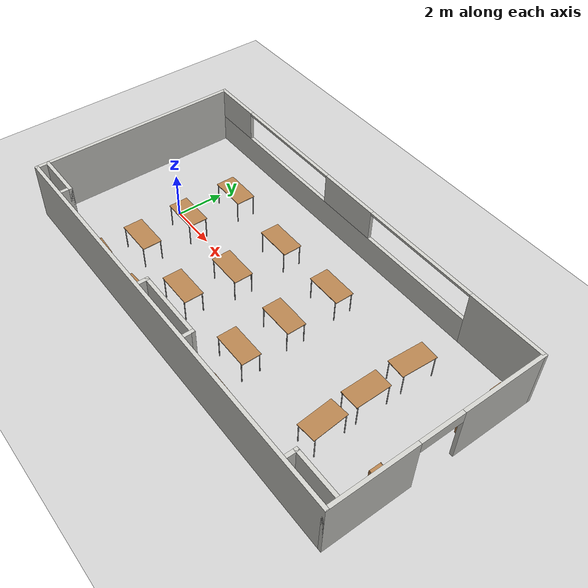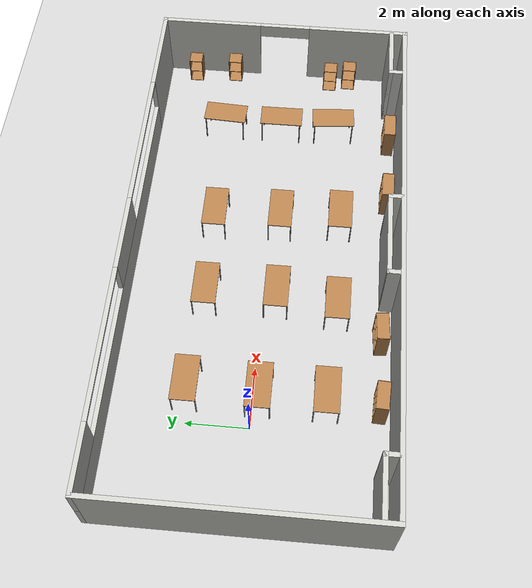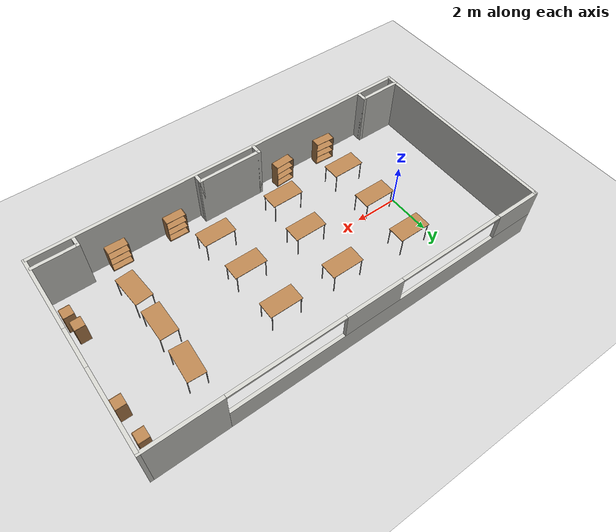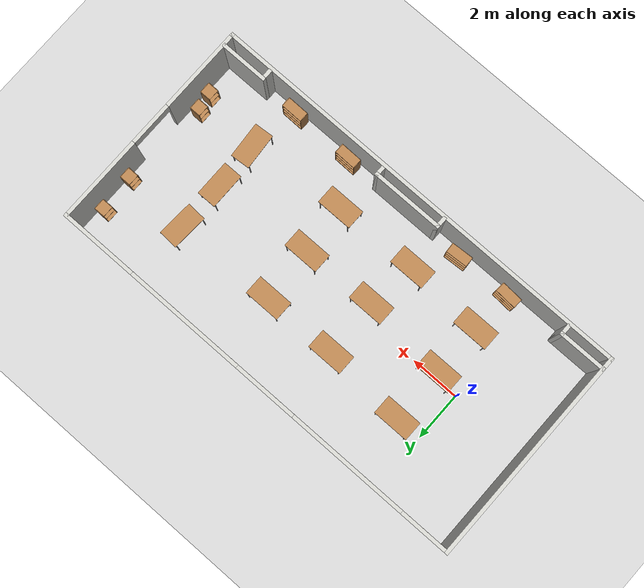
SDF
<sdf version="1.6">
 <world name="default">
  <light name="sun" type="directional">
   <pose>0 0 10 0 -0 0</pose>
   <diffuse>0.8 0.8 0.8 1</diffuse>
   <specular>0.2 0.2 0.2 1</specular>
   <attenuation>
    <range>1000</range>
    <constant>0.9</constant>
    <linear>0.01</linear>
    <quadratic>0.001</quadratic>
   </attenuation>
   <direction>-0.5 0.1 -0.9</direction>
  </light>
  <model name="ground_plane">
   <static>1</static>
   <link name="link">
    <collision name="collision">
     <geometry><plane><normal>0 0 1</normal><size>100 100</size></plane></geometry>
     <surface>
      <contact><collide_bitmask>65535</collide_bitmask></contact>
      <friction><ode><mu>100</mu><mu2>50</mu2></ode></friction>
     </surface>
    </collision>
    <visual name="visual">
     <cast_shadows>0</cast_shadows>
     <geometry><plane><normal>0 0 1</normal><size>100 100</size></plane></geometry>
     <material>
      <script><uri>file://media/materials/scripts/gazebo.material</uri><name>Gazebo/Grey</name></script>
     </material>
    </visual>
   </link>
  </model>
  <gravity>0 0 -9.8</gravity>
  <magnetic_field>6e-06 2.3e-05 -4.2e-05</magnetic_field>
  <atmosphere type="adiabatic"/>
  <physics name="default_physics" default="0" type="ode">
   <max_step_size>0.001</max_step_size>
   <real_time_factor>1</real_time_factor>
   <real_time_update_rate>1000</real_time_update_rate>
  </physics>
  <scene><ambient>0.4 0.4 0.4 1</ambient><background>0.7 0.7 0.7 1</background><shadows>1</shadows></scene>
  <audio><device>default</device></audio>
  <spherical_coordinates>
   <surface_model>EARTH_WGS84</surface_model>
   <latitude_deg>0</latitude_deg>
   <longitude_deg>0</longitude_deg>
   <elevation>0</elevation>
   <heading_deg>0</heading_deg>
  </spherical_coordinates>
  <model name="lab_room">
   <pose>5.75394 0.057613 0 0 -0 0</pose>
   <link name="Wall_1">
    <collision name="Wall_1_Collision">
     <geometry><box><size>9 0.15 2.5</size></box></geometry>
     <pose>0 0 1.25 0 -0 0</pose>
    </collision>
    <visual name="Wall_1_Visual">
     <pose>0 0 1.25 0 -0 0</pose>
     <geometry><box><size>9 0.15 2.5</size></box></geometry>
     <material>
      <script><uri>file://media/materials/scripts/gazebo.material</uri><name>Gazebo/CeilingTiled</name></script>
      <ambient>1 1 1 1</ambient>
     </material>
     <meta><layer>0</layer></meta>
    </visual>
    <pose>-8.925 0 0 0 -0 -1.5708</pose>
   </link>
   <link name="Wall_10">
    <collision name="Wall_10_Collision">
     <geometry><box><size>0.5 0.15 2.5</size></box></geometry>
     <pose>0 0 1.25 0 -0 0</pose>
    </collision>
    <visual name="Wall_10_Visual">
     <pose>0 0 1.25 0 -0 0</pose>
     <geometry><box><size>0.5 0.15 2.5</size></box></geometry>
     <material>
      <script><uri>file://media/materials/scripts/gazebo.material</uri><name>Gazebo/CeilingTiled</name></script>
      <ambient>1 1 1 1</ambient>
     </material>
     <meta><layer>0</layer></meta>
    </visual>
    <pose>7.0054 -4.11725 0 0 -0 -1.5708</pose>
   </link>
   <link name="Wall_12">
    <collision name="Wall_12_Collision">
     <geometry><box><size>0.5 0.15 2.5</size></box></geometry>
     <pose>0 0 1.25 0 -0 0</pose>
    </collision>
    <visual name="Wall_12_Visual">
     <pose>0 0 1.25 0 -0 0</pose>
     <geometry><box><size>0.5 0.15 2.5</size></box></geometry>
     <material>
      <script><uri>file://media/materials/scripts/gazebo.material</uri><name>Gazebo/CeilingTiled</name></script>
      <ambient>1 1 1 1</ambient>
     </material>
     <meta><layer>0</layer></meta>
    </visual>
    <pose>-1.26173 -4.16952 0 0 -0 1.5708</pose>
   </link>
   <link name="Wall_13">
    <collision name="Wall_13_Collision">
     <geometry><box><size>3 0.15 2.5</size></box></geometry>
     <pose>0 0 1.25 0 -0 0</pose>
    </collision>
    <visual name="Wall_13_Visual">
     <pose>0 0 1.25 0 -0 0</pose>
     <geometry><box><size>3 0.15 2.5</size></box></geometry>
     <material>
      <script><uri>file://media/materials/scripts/gazebo.material</uri><name>Gazebo/CeilingTiled</name></script>
      <ambient>1 1 1 1</ambient>
     </material>
     <meta><layer>0</layer></meta>
    </visual>
    <pose>0.163271 -3.99452 0 0 -0 0</pose>
   </link>
   <link name="Wall_14">
    <collision name="Wall_14_Collision">
     <geometry><box><size>0.5 0.15 2.5</size></box></geometry>
     <pose>0 0 1.25 0 -0 0</pose>
    </collision>
    <visual name="Wall_14_Visual">
     <pose>0 0 1.25 0 -0 0</pose>
     <geometry><box><size>0.5 0.15 2.5</size></box></geometry>
     <material>
      <script><uri>file://media/materials/scripts/gazebo.material</uri><name>Gazebo/CeilingTiled</name></script>
      <ambient>1 1 1 1</ambient>
     </material>
     <meta><layer>0</layer></meta>
    </visual>
    <pose>1.58827 -4.16952 0 0 -0 -1.5708</pose>
   </link>
   <link name="Wall_16">
    <collision name="Wall_16_Collision">
     <geometry><box><size>2 0.15 2.5</size></box></geometry>
     <pose>0 0 1.25 0 -0 0</pose>
    </collision>
    <visual name="Wall_16_Visual">
     <pose>0 0 1.25 0 -0 0</pose>
     <geometry><box><size>2 0.15 2.5</size></box></geometry>
     <material>
      <script><uri>file://media/materials/scripts/gazebo.material</uri><name>Gazebo/CeilingTiled</name></script>
      <ambient>1 1 1 1</ambient>
     </material>
     <meta><layer>0</layer></meta>
    </visual>
    <pose>-7.97989 -3.96236 0 0 -0 0</pose>
   </link>
   <link name="Wall_17">
    <collision name="Wall_17_Collision">
     <geometry><box><size>0.5 0.15 2.5</size></box></geometry>
     <pose>0 0 1.25 0 -0 0</pose>
    </collision>
    <visual name="Wall_17_Visual">
     <pose>0 0 1.25 0 -0 0</pose>
     <geometry><box><size>0.5 0.15 2.5</size></box></geometry>
     <material>
      <script><uri>file://media/materials/scripts/gazebo.material</uri><name>Gazebo/CeilingTiled</name></script>
      <ambient>1 1 1 1</ambient>
     </material>
     <meta><layer>0</layer></meta>
    </visual>
    <pose>-7.05489 -4.13736 0 0 -0 -1.5708</pose>
   </link>
   <link name="Wall_2">
    <collision name="Wall_2_Collision">
     <geometry><box><size>18 0.15 2.5</size></box></geometry>
     <pose>0 0 1.25 0 -0 0</pose>
    </collision>
    <visual name="Wall_2_Visual">
     <pose>0 0 1.25 0 -0 0</pose>
     <geometry><box><size>18 0.15 2.5</size></box></geometry>
     <material>
      <script><uri>file://media/materials/scripts/gazebo.material</uri><name>Gazebo/CeilingTiled</name></script>
      <ambient>1 1 1 1</ambient>
     </material>
     <meta><layer>0</layer></meta>
    </visual>
    <pose>0 -4.425 0 0 -0 0</pose>
   </link>
   <link name="Wall_3">
    <pose>8.925 0 0 0 -0 1.5708</pose>
    <visual name="Wall_3_Visual_0">
     <pose>-2.71005 0 1.25 0 -0 0</pose>
     <geometry><box><size>3.5799 0.15 2.5</size></box></geometry>
     <material>
      <script><uri>file://media/materials/scripts/gazebo.material</uri><name>Gazebo/CeilingTiled</name></script>
      <ambient>1 1 1 1</ambient>
     </material>
     <meta><layer>0</layer></meta>
    </visual>
    <collision name="Wall_3_Collision_0">
     <geometry><box><size>3.5799 0.15 2.5</size></box></geometry>
     <pose>-2.71005 0 1.25 0 -0 0</pose>
    </collision>
    <visual name="Wall_3_Visual_1">
     <pose>2.68995 0 1.25 0 -0 0</pose>
     <geometry><box><size>3.6201 0.15 2.5</size></box></geometry>
     <material>
      <script><uri>file://media/materials/scripts/gazebo.material</uri><name>Gazebo/CeilingTiled</name></script>
      <ambient>1 1 1 1</ambient>
     </material>
     <meta><layer>0</layer></meta>
    </visual>
    <collision name="Wall_3_Collision_1">
     <geometry><box><size>3.6201 0.15 2.5</size></box></geometry>
     <pose>2.68995 0 1.25 0 -0 0</pose>
    </collision>
    <visual name="Wall_3_Visual_2">
     <pose>-0.020099 0 2.25 0 -0 0</pose>
     <geometry><box><size>1.8 0.15 0.5</size></box></geometry>
     <material>
      <script><uri>file://media/materials/scripts/gazebo.material</uri><name>Gazebo/CeilingTiled</name></script>
      <ambient>1 1 1 1</ambient>
     </material>
     <meta><layer>0</layer></meta>
    </visual>
    <collision name="Wall_3_Collision_2">
     <geometry><box><size>1.8 0.15 0.5</size></box></geometry>
     <pose>-0.020099 0 2.25 0 -0 0</pose>
    </collision>
   </link>
   <link name="Wall_4">
    <pose>0 4.425 0 0 -0 3.14159</pose>
    <visual name="Wall_4_Visual_0">
     <pose>-7.38191 0 1.25 0 -0 0</pose>
     <geometry><box><size>3.23617 0.15 2.5</size></box></geometry>
     <material>
      <script><uri>file://media/materials/scripts/gazebo.material</uri><name>Gazebo/CeilingTiled</name></script>
      <ambient>1 1 1 1</ambient>
     </material>
     <meta><layer>0</layer></meta>
    </visual>
    <collision name="Wall_4_Collision_0">
     <geometry><box><size>3.23617 0.15 2.5</size></box></geometry>
     <pose>-7.38191 0 1.25 0 -0 0</pose>
    </collision>
    <visual name="Wall_4_Visual_1">
     <pose>1.61809 0 0.6 0 -0 0</pose>
     <geometry><box><size>14.7638 0.15 1.2</size></box></geometry>
     <material>
      <script><uri>file://media/materials/scripts/gazebo.material</uri><name>Gazebo/CeilingTiled</name></script>
      <ambient>1 1 1 1</ambient>
     </material>
     <meta><layer>0</layer></meta>
    </visual>
    <collision name="Wall_4_Collision_1">
     <geometry><box><size>14.7638 0.15 1.2</size></box></geometry>
     <pose>1.61809 0 0.6 0 -0 0</pose>
    </collision>
    <visual name="Wall_4_Visual_2">
     <pose>0.547697 0 1.85 0 -0 0</pose>
     <geometry><box><size>2.62304 0.15 1.3</size></box></geometry>
     <material>
      <script><uri>file://media/materials/scripts/gazebo.material</uri><name>Gazebo/CeilingTiled</name></script>
      <ambient>1 1 1 1</ambient>
     </material>
     <meta><layer>0</layer></meta>
    </visual>
    <collision name="Wall_4_Collision_2">
     <geometry><box><size>2.62304 0.15 1.3</size></box></geometry>
     <pose>0.547697 0 1.85 0 -0 0</pose>
    </collision>
    <visual name="Wall_4_Visual_3">
     <pose>7.92961 0 1.85 0 -0 0</pose>
     <geometry><box><size>2.14078 0.15 1.3</size></box></geometry>
     <material>
      <script><uri>file://media/materials/scripts/gazebo.material</uri><name>Gazebo/CeilingTiled</name></script>
      <ambient>1 1 1 1</ambient>
     </material>
     <meta><layer>0</layer></meta>
    </visual>
    <collision name="Wall_4_Collision_3">
     <geometry><box><size>2.14078 0.15 1.3</size></box></geometry>
     <pose>7.92961 0 1.85 0 -0 0</pose>
    </collision>
    <visual name="Wall_4_Visual_4">
     <pose>-3.26383 0 2.45 0 -0 0</pose>
     <geometry><box><size>5 0.15 0.1</size></box></geometry>
     <material>
      <script><uri>file://media/materials/scripts/gazebo.material</uri><name>Gazebo/CeilingTiled</name></script>
      <ambient>1 1 1 1</ambient>
     </material>
     <meta><layer>0</layer></meta>
    </visual>
    <collision name="Wall_4_Collision_4">
     <geometry><box><size>5 0.15 0.1</size></box></geometry>
     <pose>-3.26383 0 2.45 0 -0 0</pose>
    </collision>
    <visual name="Wall_4_Visual_5">
     <pose>4.35922 0 2.45 0 -0 0</pose>
     <geometry><box><size>5 0.15 0.1</size></box></geometry>
     <material>
      <script><uri>file://media/materials/scripts/gazebo.material</uri><name>Gazebo/CeilingTiled</name></script>
      <ambient>1 1 1 1</ambient>
     </material>
     <meta><layer>0</layer></meta>
    </visual>
    <collision name="Wall_4_Collision_5">
     <geometry><box><size>5 0.15 0.1</size></box></geometry>
     <pose>4.35922 0 2.45 0 -0 0</pose>
    </collision>
   </link>
   <link name="Wall_9">
    <collision name="Wall_9_Collision">
     <geometry><box><size>2 0.15 2.5</size></box></geometry>
     <pose>0 0 1.25 0 -0 0</pose>
    </collision>
    <visual name="Wall_9_Visual">
     <pose>0 0 1.25 0 -0 0</pose>
     <geometry><box><size>2 0.15 2.5</size></box></geometry>
     <material>
      <script><uri>file://media/materials/scripts/gazebo.material</uri><name>Gazebo/CeilingTiled</name></script>
      <ambient>1 1 1 1</ambient>
     </material>
     <meta><layer>0</layer></meta>
    </visual>
    <pose>7.9304 -3.94225 0 0 -0 3.14159</pose>
   </link>
   <static>1</static>
  </model>
  <model name="table">
   <static>1</static>
   <link name="link">
    <collision name="surface">
     <pose>0 0 1 0 -0 0</pose>
     <geometry><box><size>1.5 0.8 0.03</size></box></geometry>
     <surface><friction><ode><mu>0.6</mu><mu2>0.6</mu2></ode></friction></surface>
    </collision>
    <visual name="visual1">
     <pose>0 0 1 0 -0 0</pose>
     <geometry><box><size>1.5 0.8 0.03</size></box></geometry>
     <material>
      <script><uri>file://media/materials/scripts/gazebo.material</uri><name>Gazebo/Wood</name></script>
     </material>
    </visual>
    <collision name="front_left_leg">
     <pose>0.68 0.38 0.5 0 -0 0</pose>
     <geometry><cylinder><radius>0.02</radius><length>1</length></cylinder></geometry>
    </collision>
    <visual name="front_left_leg">
     <pose>0.68 0.38 0.5 0 -0 0</pose>
     <geometry><cylinder><radius>0.02</radius><length>1</length></cylinder></geometry>
     <material>
      <script><uri>file://media/materials/scripts/gazebo.material</uri><name>Gazebo/Grey</name></script>
     </material>
    </visual>
    <collision name="front_right_leg">
     <pose>0.68 -0.38 0.5 0 -0 0</pose>
     <geometry><cylinder><radius>0.02</radius><length>1</length></cylinder></geometry>
    </collision>
    <visual name="front_right_leg">
     <pose>0.68 -0.38 0.5 0 -0 0</pose>
     <geometry><cylinder><radius>0.02</radius><length>1</length></cylinder></geometry>
     <material>
      <script><uri>file://media/materials/scripts/gazebo.material</uri><name>Gazebo/Grey</name></script>
     </material>
    </visual>
    <collision name="back_right_leg">
     <pose>-0.68 -0.38 0.5 0 -0 0</pose>
     <geometry><cylinder><radius>0.02</radius><length>1</length></cylinder></geometry>
    </collision>
    <visual name="back_right_leg">
     <pose>-0.68 -0.38 0.5 0 -0 0</pose>
     <geometry><cylinder><radius>0.02</radius><length>1</length></cylinder></geometry>
     <material>
      <script><uri>file://media/materials/scripts/gazebo.material</uri><name>Gazebo/Grey</name></script>
     </material>
    </visual>
    <collision name="back_left_leg">
     <pose>-0.68 0.38 0.5 0 -0 0</pose>
     <geometry><cylinder><radius>0.02</radius><length>1</length></cylinder></geometry>
    </collision>
    <visual name="back_left_leg">
     <pose>-0.68 0.38 0.5 0 -0 0</pose>
     <geometry><cylinder><radius>0.02</radius><length>1</length></cylinder></geometry>
     <material>
      <script><uri>file://media/materials/scripts/gazebo.material</uri><name>Gazebo/Grey</name></script>
     </material>
    </visual>
   </link>
   <pose>1.08189 -2.2938 0 0 -0 0</pose>
  </model>
  <model name="table_0">
   <static>1</static>
   <link name="link">
    <collision name="surface">
     <pose>0 0 1 0 -0 0</pose>
     <geometry><box><size>1.5 0.8 0.03</size></box></geometry>
     <surface><friction><ode><mu>0.6</mu><mu2>0.6</mu2></ode></friction></surface>
    </collision>
    <visual name="visual1">
     <pose>0 0 1 0 -0 0</pose>
     <geometry><box><size>1.5 0.8 0.03</size></box></geometry>
     <material>
      <script><uri>file://media/materials/scripts/gazebo.material</uri><name>Gazebo/Wood</name></script>
     </material>
    </visual>
    <collision name="front_left_leg">
     <pose>0.68 0.38 0.5 0 -0 0</pose>
     <geometry><cylinder><radius>0.02</radius><length>1</length></cylinder></geometry>
    </collision>
    <visual name="front_left_leg">
     <pose>0.68 0.38 0.5 0 -0 0</pose>
     <geometry><cylinder><radius>0.02</radius><length>1</length></cylinder></geometry>
     <material>
      <script><uri>file://media/materials/scripts/gazebo.material</uri><name>Gazebo/Grey</name></script>
     </material>
    </visual>
    <collision name="front_right_leg">
     <pose>0.68 -0.38 0.5 0 -0 0</pose>
     <geometry><cylinder><radius>0.02</radius><length>1</length></cylinder></geometry>
    </collision>
    <visual name="front_right_leg">
     <pose>0.68 -0.38 0.5 0 -0 0</pose>
     <geometry><cylinder><radius>0.02</radius><length>1</length></cylinder></geometry>
     <material>
      <script><uri>file://media/materials/scripts/gazebo.material</uri><name>Gazebo/Grey</name></script>
     </material>
    </visual>
    <collision name="back_right_leg">
     <pose>-0.68 -0.38 0.5 0 -0 0</pose>
     <geometry><cylinder><radius>0.02</radius><length>1</length></cylinder></geometry>
    </collision>
    <visual name="back_right_leg">
     <pose>-0.68 -0.38 0.5 0 -0 0</pose>
     <geometry><cylinder><radius>0.02</radius><length>1</length></cylinder></geometry>
     <material>
      <script><uri>file://media/materials/scripts/gazebo.material</uri><name>Gazebo/Grey</name></script>
     </material>
    </visual>
    <collision name="back_left_leg">
     <pose>-0.68 0.38 0.5 0 -0 0</pose>
     <geometry><cylinder><radius>0.02</radius><length>1</length></cylinder></geometry>
    </collision>
    <visual name="back_left_leg">
     <pose>-0.68 0.38 0.5 0 -0 0</pose>
     <geometry><cylinder><radius>0.02</radius><length>1</length></cylinder></geometry>
     <material>
      <script><uri>file://media/materials/scripts/gazebo.material</uri><name>Gazebo/Grey</name></script>
     </material>
    </visual>
   </link>
   <pose>1.06456 -0.205149 0 0 -0 0</pose>
  </model>
  <model name="table_1">
   <static>1</static>
   <link name="link">
    <collision name="surface">
     <pose>0 0 1 0 -0 0</pose>
     <geometry><box><size>1.5 0.8 0.03</size></box></geometry>
     <surface><friction><ode><mu>0.6</mu><mu2>0.6</mu2></ode></friction></surface>
    </collision>
    <visual name="visual1">
     <pose>0 0 1 0 -0 0</pose>
     <geometry><box><size>1.5 0.8 0.03</size></box></geometry>
     <material>
      <script><uri>file://media/materials/scripts/gazebo.material</uri><name>Gazebo/Wood</name></script>
     </material>
    </visual>
    <collision name="front_left_leg">
     <pose>0.68 0.38 0.5 0 -0 0</pose>
     <geometry><cylinder><radius>0.02</radius><length>1</length></cylinder></geometry>
    </collision>
    <visual name="front_left_leg">
     <pose>0.68 0.38 0.5 0 -0 0</pose>
     <geometry><cylinder><radius>0.02</radius><length>1</length></cylinder></geometry>
     <material>
      <script><uri>file://media/materials/scripts/gazebo.material</uri><name>Gazebo/Grey</name></script>
     </material>
    </visual>
    <collision name="front_right_leg">
     <pose>0.68 -0.38 0.5 0 -0 0</pose>
     <geometry><cylinder><radius>0.02</radius><length>1</length></cylinder></geometry>
    </collision>
    <visual name="front_right_leg">
     <pose>0.68 -0.38 0.5 0 -0 0</pose>
     <geometry><cylinder><radius>0.02</radius><length>1</length></cylinder></geometry>
     <material>
      <script><uri>file://media/materials/scripts/gazebo.material</uri><name>Gazebo/Grey</name></script>
     </material>
    </visual>
    <collision name="back_right_leg">
     <pose>-0.68 -0.38 0.5 0 -0 0</pose>
     <geometry><cylinder><radius>0.02</radius><length>1</length></cylinder></geometry>
    </collision>
    <visual name="back_right_leg">
     <pose>-0.68 -0.38 0.5 0 -0 0</pose>
     <geometry><cylinder><radius>0.02</radius><length>1</length></cylinder></geometry>
     <material>
      <script><uri>file://media/materials/scripts/gazebo.material</uri><name>Gazebo/Grey</name></script>
     </material>
    </visual>
    <collision name="back_left_leg">
     <pose>-0.68 0.38 0.5 0 -0 0</pose>
     <geometry><cylinder><radius>0.02</radius><length>1</length></cylinder></geometry>
    </collision>
    <visual name="back_left_leg">
     <pose>-0.68 0.38 0.5 0 -0 0</pose>
     <geometry><cylinder><radius>0.02</radius><length>1</length></cylinder></geometry>
     <material>
      <script><uri>file://media/materials/scripts/gazebo.material</uri><name>Gazebo/Grey</name></script>
     </material>
    </visual>
   </link>
   <pose>1.09796 2.05913 0 0 -0 0</pose>
  </model>
  <model name="table_2">
   <static>1</static>
   <link name="link">
    <collision name="surface">
     <pose>0 0 1 0 -0 0</pose>
     <geometry><box><size>1.5 0.8 0.03</size></box></geometry>
     <surface><friction><ode><mu>0.6</mu><mu2>0.6</mu2></ode></friction></surface>
    </collision>
    <visual name="visual1">
     <pose>0 0 1 0 -0 0</pose>
     <geometry><box><size>1.5 0.8 0.03</size></box></geometry>
     <material>
      <script><uri>file://media/materials/scripts/gazebo.material</uri><name>Gazebo/Wood</name></script>
     </material>
    </visual>
    <collision name="front_left_leg">
     <pose>0.68 0.38 0.5 0 -0 0</pose>
     <geometry><cylinder><radius>0.02</radius><length>1</length></cylinder></geometry>
    </collision>
    <visual name="front_left_leg">
     <pose>0.68 0.38 0.5 0 -0 0</pose>
     <geometry><cylinder><radius>0.02</radius><length>1</length></cylinder></geometry>
     <material>
      <script><uri>file://media/materials/scripts/gazebo.material</uri><name>Gazebo/Grey</name></script>
     </material>
    </visual>
    <collision name="front_right_leg">
     <pose>0.68 -0.38 0.5 0 -0 0</pose>
     <geometry><cylinder><radius>0.02</radius><length>1</length></cylinder></geometry>
    </collision>
    <visual name="front_right_leg">
     <pose>0.68 -0.38 0.5 0 -0 0</pose>
     <geometry><cylinder><radius>0.02</radius><length>1</length></cylinder></geometry>
     <material>
      <script><uri>file://media/materials/scripts/gazebo.material</uri><name>Gazebo/Grey</name></script>
     </material>
    </visual>
    <collision name="back_right_leg">
     <pose>-0.68 -0.38 0.5 0 -0 0</pose>
     <geometry><cylinder><radius>0.02</radius><length>1</length></cylinder></geometry>
    </collision>
    <visual name="back_right_leg">
     <pose>-0.68 -0.38 0.5 0 -0 0</pose>
     <geometry><cylinder><radius>0.02</radius><length>1</length></cylinder></geometry>
     <material>
      <script><uri>file://media/materials/scripts/gazebo.material</uri><name>Gazebo/Grey</name></script>
     </material>
    </visual>
    <collision name="back_left_leg">
     <pose>-0.68 0.38 0.5 0 -0 0</pose>
     <geometry><cylinder><radius>0.02</radius><length>1</length></cylinder></geometry>
    </collision>
    <visual name="back_left_leg">
     <pose>-0.68 0.38 0.5 0 -0 0</pose>
     <geometry><cylinder><radius>0.02</radius><length>1</length></cylinder></geometry>
     <material>
      <script><uri>file://media/materials/scripts/gazebo.material</uri><name>Gazebo/Grey</name></script>
     </material>
    </visual>
   </link>
   <pose>4.46085 1.83924 0 0 -0 0</pose>
  </model>
  <model name="table_3">
   <static>1</static>
   <link name="link">
    <collision name="surface">
     <pose>0 0 1 0 -0 0</pose>
     <geometry><box><size>1.5 0.8 0.03</size></box></geometry>
     <surface><friction><ode><mu>0.6</mu><mu2>0.6</mu2></ode></friction></surface>
    </collision>
    <visual name="visual1">
     <pose>0 0 1 0 -0 0</pose>
     <geometry><box><size>1.5 0.8 0.03</size></box></geometry>
     <material>
      <script><uri>file://media/materials/scripts/gazebo.material</uri><name>Gazebo/Wood</name></script>
     </material>
    </visual>
    <collision name="front_left_leg">
     <pose>0.68 0.38 0.5 0 -0 0</pose>
     <geometry><cylinder><radius>0.02</radius><length>1</length></cylinder></geometry>
    </collision>
    <visual name="front_left_leg">
     <pose>0.68 0.38 0.5 0 -0 0</pose>
     <geometry><cylinder><radius>0.02</radius><length>1</length></cylinder></geometry>
     <material>
      <script><uri>file://media/materials/scripts/gazebo.material</uri><name>Gazebo/Grey</name></script>
     </material>
    </visual>
    <collision name="front_right_leg">
     <pose>0.68 -0.38 0.5 0 -0 0</pose>
     <geometry><cylinder><radius>0.02</radius><length>1</length></cylinder></geometry>
    </collision>
    <visual name="front_right_leg">
     <pose>0.68 -0.38 0.5 0 -0 0</pose>
     <geometry><cylinder><radius>0.02</radius><length>1</length></cylinder></geometry>
     <material>
      <script><uri>file://media/materials/scripts/gazebo.material</uri><name>Gazebo/Grey</name></script>
     </material>
    </visual>
    <collision name="back_right_leg">
     <pose>-0.68 -0.38 0.5 0 -0 0</pose>
     <geometry><cylinder><radius>0.02</radius><length>1</length></cylinder></geometry>
    </collision>
    <visual name="back_right_leg">
     <pose>-0.68 -0.38 0.5 0 -0 0</pose>
     <geometry><cylinder><radius>0.02</radius><length>1</length></cylinder></geometry>
     <material>
      <script><uri>file://media/materials/scripts/gazebo.material</uri><name>Gazebo/Grey</name></script>
     </material>
    </visual>
    <collision name="back_left_leg">
     <pose>-0.68 0.38 0.5 0 -0 0</pose>
     <geometry><cylinder><radius>0.02</radius><length>1</length></cylinder></geometry>
    </collision>
    <visual name="back_left_leg">
     <pose>-0.68 0.38 0.5 0 -0 0</pose>
     <geometry><cylinder><radius>0.02</radius><length>1</length></cylinder></geometry>
     <material>
      <script><uri>file://media/materials/scripts/gazebo.material</uri><name>Gazebo/Grey</name></script>
     </material>
    </visual>
   </link>
   <pose>4.53977 -0.479619 0 0 -0 0</pose>
  </model>
  <model name="table_4">
   <static>1</static>
   <link name="link">
    <collision name="surface">
     <pose>0 0 1 0 -0 0</pose>
     <geometry><box><size>1.5 0.8 0.03</size></box></geometry>
     <surface><friction><ode><mu>0.6</mu><mu2>0.6</mu2></ode></friction></surface>
    </collision>
    <visual name="visual1">
     <pose>0 0 1 0 -0 0</pose>
     <geometry><box><size>1.5 0.8 0.03</size></box></geometry>
     <material>
      <script><uri>file://media/materials/scripts/gazebo.material</uri><name>Gazebo/Wood</name></script>
     </material>
    </visual>
    <collision name="front_left_leg">
     <pose>0.68 0.38 0.5 0 -0 0</pose>
     <geometry><cylinder><radius>0.02</radius><length>1</length></cylinder></geometry>
    </collision>
    <visual name="front_left_leg">
     <pose>0.68 0.38 0.5 0 -0 0</pose>
     <geometry><cylinder><radius>0.02</radius><length>1</length></cylinder></geometry>
     <material>
      <script><uri>file://media/materials/scripts/gazebo.material</uri><name>Gazebo/Grey</name></script>
     </material>
    </visual>
    <collision name="front_right_leg">
     <pose>0.68 -0.38 0.5 0 -0 0</pose>
     <geometry><cylinder><radius>0.02</radius><length>1</length></cylinder></geometry>
    </collision>
    <visual name="front_right_leg">
     <pose>0.68 -0.38 0.5 0 -0 0</pose>
     <geometry><cylinder><radius>0.02</radius><length>1</length></cylinder></geometry>
     <material>
      <script><uri>file://media/materials/scripts/gazebo.material</uri><name>Gazebo/Grey</name></script>
     </material>
    </visual>
    <collision name="back_right_leg">
     <pose>-0.68 -0.38 0.5 0 -0 0</pose>
     <geometry><cylinder><radius>0.02</radius><length>1</length></cylinder></geometry>
    </collision>
    <visual name="back_right_leg">
     <pose>-0.68 -0.38 0.5 0 -0 0</pose>
     <geometry><cylinder><radius>0.02</radius><length>1</length></cylinder></geometry>
     <material>
      <script><uri>file://media/materials/scripts/gazebo.material</uri><name>Gazebo/Grey</name></script>
     </material>
    </visual>
    <collision name="back_left_leg">
     <pose>-0.68 0.38 0.5 0 -0 0</pose>
     <geometry><cylinder><radius>0.02</radius><length>1</length></cylinder></geometry>
    </collision>
    <visual name="back_left_leg">
     <pose>-0.68 0.38 0.5 0 -0 0</pose>
     <geometry><cylinder><radius>0.02</radius><length>1</length></cylinder></geometry>
     <material>
      <script><uri>file://media/materials/scripts/gazebo.material</uri><name>Gazebo/Grey</name></script>
     </material>
    </visual>
   </link>
   <pose>4.27247 -2.47329 0 0 -0 0</pose>
  </model>
  <model name="table_5">
   <static>1</static>
   <link name="link">
    <collision name="surface">
     <pose>0 0 1 0 -0 0</pose>
     <geometry><box><size>1.5 0.8 0.03</size></box></geometry>
     <surface><friction><ode><mu>0.6</mu><mu2>0.6</mu2></ode></friction></surface>
    </collision>
    <visual name="visual1">
     <pose>0 0 1 0 -0 0</pose>
     <geometry><box><size>1.5 0.8 0.03</size></box></geometry>
     <material>
      <script><uri>file://media/materials/scripts/gazebo.material</uri><name>Gazebo/Wood</name></script>
     </material>
    </visual>
    <collision name="front_left_leg">
     <pose>0.68 0.38 0.5 0 -0 0</pose>
     <geometry><cylinder><radius>0.02</radius><length>1</length></cylinder></geometry>
    </collision>
    <visual name="front_left_leg">
     <pose>0.68 0.38 0.5 0 -0 0</pose>
     <geometry><cylinder><radius>0.02</radius><length>1</length></cylinder></geometry>
     <material>
      <script><uri>file://media/materials/scripts/gazebo.material</uri><name>Gazebo/Grey</name></script>
     </material>
    </visual>
    <collision name="front_right_leg">
     <pose>0.68 -0.38 0.5 0 -0 0</pose>
     <geometry><cylinder><radius>0.02</radius><length>1</length></cylinder></geometry>
    </collision>
    <visual name="front_right_leg">
     <pose>0.68 -0.38 0.5 0 -0 0</pose>
     <geometry><cylinder><radius>0.02</radius><length>1</length></cylinder></geometry>
     <material>
      <script><uri>file://media/materials/scripts/gazebo.material</uri><name>Gazebo/Grey</name></script>
     </material>
    </visual>
    <collision name="back_right_leg">
     <pose>-0.68 -0.38 0.5 0 -0 0</pose>
     <geometry><cylinder><radius>0.02</radius><length>1</length></cylinder></geometry>
    </collision>
    <visual name="back_right_leg">
     <pose>-0.68 -0.38 0.5 0 -0 0</pose>
     <geometry><cylinder><radius>0.02</radius><length>1</length></cylinder></geometry>
     <material>
      <script><uri>file://media/materials/scripts/gazebo.material</uri><name>Gazebo/Grey</name></script>
     </material>
    </visual>
    <collision name="back_left_leg">
     <pose>-0.68 0.38 0.5 0 -0 0</pose>
     <geometry><cylinder><radius>0.02</radius><length>1</length></cylinder></geometry>
    </collision>
    <visual name="back_left_leg">
     <pose>-0.68 0.38 0.5 0 -0 0</pose>
     <geometry><cylinder><radius>0.02</radius><length>1</length></cylinder></geometry>
     <material>
      <script><uri>file://media/materials/scripts/gazebo.material</uri><name>Gazebo/Grey</name></script>
     </material>
    </visual>
   </link>
   <pose>7.72959 -2.41186 0 0 -0 0</pose>
  </model>
  <model name="table_6">
   <static>1</static>
   <link name="link">
    <collision name="surface">
     <pose>0 0 1 0 -0 0</pose>
     <geometry><box><size>1.5 0.8 0.03</size></box></geometry>
     <surface><friction><ode><mu>0.6</mu><mu2>0.6</mu2></ode></friction></surface>
    </collision>
    <visual name="visual1">
     <pose>0 0 1 0 -0 0</pose>
     <geometry><box><size>1.5 0.8 0.03</size></box></geometry>
     <material>
      <script><uri>file://media/materials/scripts/gazebo.material</uri><name>Gazebo/Wood</name></script>
     </material>
    </visual>
    <collision name="front_left_leg">
     <pose>0.68 0.38 0.5 0 -0 0</pose>
     <geometry><cylinder><radius>0.02</radius><length>1</length></cylinder></geometry>
    </collision>
    <visual name="front_left_leg">
     <pose>0.68 0.38 0.5 0 -0 0</pose>
     <geometry><cylinder><radius>0.02</radius><length>1</length></cylinder></geometry>
     <material>
      <script><uri>file://media/materials/scripts/gazebo.material</uri><name>Gazebo/Grey</name></script>
     </material>
    </visual>
    <collision name="front_right_leg">
     <pose>0.68 -0.38 0.5 0 -0 0</pose>
     <geometry><cylinder><radius>0.02</radius><length>1</length></cylinder></geometry>
    </collision>
    <visual name="front_right_leg">
     <pose>0.68 -0.38 0.5 0 -0 0</pose>
     <geometry><cylinder><radius>0.02</radius><length>1</length></cylinder></geometry>
     <material>
      <script><uri>file://media/materials/scripts/gazebo.material</uri><name>Gazebo/Grey</name></script>
     </material>
    </visual>
    <collision name="back_right_leg">
     <pose>-0.68 -0.38 0.5 0 -0 0</pose>
     <geometry><cylinder><radius>0.02</radius><length>1</length></cylinder></geometry>
    </collision>
    <visual name="back_right_leg">
     <pose>-0.68 -0.38 0.5 0 -0 0</pose>
     <geometry><cylinder><radius>0.02</radius><length>1</length></cylinder></geometry>
     <material>
      <script><uri>file://media/materials/scripts/gazebo.material</uri><name>Gazebo/Grey</name></script>
     </material>
    </visual>
    <collision name="back_left_leg">
     <pose>-0.68 0.38 0.5 0 -0 0</pose>
     <geometry><cylinder><radius>0.02</radius><length>1</length></cylinder></geometry>
    </collision>
    <visual name="back_left_leg">
     <pose>-0.68 0.38 0.5 0 -0 0</pose>
     <geometry><cylinder><radius>0.02</radius><length>1</length></cylinder></geometry>
     <material>
      <script><uri>file://media/materials/scripts/gazebo.material</uri><name>Gazebo/Grey</name></script>
     </material>
    </visual>
   </link>
   <pose>7.58183 -0.377991 0 0 -0 0</pose>
  </model>
  <model name="table_7">
   <static>1</static>
   <link name="link">
    <collision name="surface">
     <pose>0 0 1 0 -0 0</pose>
     <geometry><box><size>1.5 0.8 0.03</size></box></geometry>
     <surface><friction><ode><mu>0.6</mu><mu2>0.6</mu2></ode></friction></surface>
    </collision>
    <visual name="visual1">
     <pose>0 0 1 0 -0 0</pose>
     <geometry><box><size>1.5 0.8 0.03</size></box></geometry>
     <material>
      <script><uri>file://media/materials/scripts/gazebo.material</uri><name>Gazebo/Wood</name></script>
     </material>
    </visual>
    <collision name="front_left_leg">
     <pose>0.68 0.38 0.5 0 -0 0</pose>
     <geometry><cylinder><radius>0.02</radius><length>1</length></cylinder></geometry>
    </collision>
    <visual name="front_left_leg">
     <pose>0.68 0.38 0.5 0 -0 0</pose>
     <geometry><cylinder><radius>0.02</radius><length>1</length></cylinder></geometry>
     <material>
      <script><uri>file://media/materials/scripts/gazebo.material</uri><name>Gazebo/Grey</name></script>
     </material>
    </visual>
    <collision name="front_right_leg">
     <pose>0.68 -0.38 0.5 0 -0 0</pose>
     <geometry><cylinder><radius>0.02</radius><length>1</length></cylinder></geometry>
    </collision>
    <visual name="front_right_leg">
     <pose>0.68 -0.38 0.5 0 -0 0</pose>
     <geometry><cylinder><radius>0.02</radius><length>1</length></cylinder></geometry>
     <material>
      <script><uri>file://media/materials/scripts/gazebo.material</uri><name>Gazebo/Grey</name></script>
     </material>
    </visual>
    <collision name="back_right_leg">
     <pose>-0.68 -0.38 0.5 0 -0 0</pose>
     <geometry><cylinder><radius>0.02</radius><length>1</length></cylinder></geometry>
    </collision>
    <visual name="back_right_leg">
     <pose>-0.68 -0.38 0.5 0 -0 0</pose>
     <geometry><cylinder><radius>0.02</radius><length>1</length></cylinder></geometry>
     <material>
      <script><uri>file://media/materials/scripts/gazebo.material</uri><name>Gazebo/Grey</name></script>
     </material>
    </visual>
    <collision name="back_left_leg">
     <pose>-0.68 0.38 0.5 0 -0 0</pose>
     <geometry><cylinder><radius>0.02</radius><length>1</length></cylinder></geometry>
    </collision>
    <visual name="back_left_leg">
     <pose>-0.68 0.38 0.5 0 -0 0</pose>
     <geometry><cylinder><radius>0.02</radius><length>1</length></cylinder></geometry>
     <material>
      <script><uri>file://media/materials/scripts/gazebo.material</uri><name>Gazebo/Grey</name></script>
     </material>
    </visual>
   </link>
   <pose>7.47591 1.86545 0 0 -0 0</pose>
  </model>
  <model name="table_8">
   <static>1</static>
   <link name="link">
    <collision name="surface">
     <pose>0 0 1 0 -0 0</pose>
     <geometry><box><size>1.5 0.8 0.03</size></box></geometry>
     <surface><friction><ode><mu>0.6</mu><mu2>0.6</mu2></ode></friction></surface>
    </collision>
    <visual name="visual1">
     <pose>0 0 1 0 -0 0</pose>
     <geometry><box><size>1.5 0.8 0.03</size></box></geometry>
     <material>
      <script><uri>file://media/materials/scripts/gazebo.material</uri><name>Gazebo/Wood</name></script>
     </material>
    </visual>
    <collision name="front_left_leg">
     <pose>0.68 0.38 0.5 0 -0 0</pose>
     <geometry><cylinder><radius>0.02</radius><length>1</length></cylinder></geometry>
    </collision>
    <visual name="front_left_leg">
     <pose>0.68 0.38 0.5 0 -0 0</pose>
     <geometry><cylinder><radius>0.02</radius><length>1</length></cylinder></geometry>
     <material>
      <script><uri>file://media/materials/scripts/gazebo.material</uri><name>Gazebo/Grey</name></script>
     </material>
    </visual>
    <collision name="front_right_leg">
     <pose>0.68 -0.38 0.5 0 -0 0</pose>
     <geometry><cylinder><radius>0.02</radius><length>1</length></cylinder></geometry>
    </collision>
    <visual name="front_right_leg">
     <pose>0.68 -0.38 0.5 0 -0 0</pose>
     <geometry><cylinder><radius>0.02</radius><length>1</length></cylinder></geometry>
     <material>
      <script><uri>file://media/materials/scripts/gazebo.material</uri><name>Gazebo/Grey</name></script>
     </material>
    </visual>
    <collision name="back_right_leg">
     <pose>-0.68 -0.38 0.5 0 -0 0</pose>
     <geometry><cylinder><radius>0.02</radius><length>1</length></cylinder></geometry>
    </collision>
    <visual name="back_right_leg">
     <pose>-0.68 -0.38 0.5 0 -0 0</pose>
     <geometry><cylinder><radius>0.02</radius><length>1</length></cylinder></geometry>
     <material>
      <script><uri>file://media/materials/scripts/gazebo.material</uri><name>Gazebo/Grey</name></script>
     </material>
    </visual>
    <collision name="back_left_leg">
     <pose>-0.68 0.38 0.5 0 -0 0</pose>
     <geometry><cylinder><radius>0.02</radius><length>1</length></cylinder></geometry>
    </collision>
    <visual name="back_left_leg">
     <pose>-0.68 0.38 0.5 0 -0 0</pose>
     <geometry><cylinder><radius>0.02</radius><length>1</length></cylinder></geometry>
     <material>
      <script><uri>file://media/materials/scripts/gazebo.material</uri><name>Gazebo/Grey</name></script>
     </material>
    </visual>
   </link>
   <pose>11.6453 1.95401 0 0 0 -1.62653</pose>
  </model>
  <model name="table_9">
   <static>1</static>
   <link name="link">
    <collision name="surface">
     <pose>0 0 1 0 -0 0</pose>
     <geometry><box><size>1.5 0.8 0.03</size></box></geometry>
     <surface><friction><ode><mu>0.6</mu><mu2>0.6</mu2></ode></friction></surface>
    </collision>
    <visual name="visual1">
     <pose>0 0 1 0 -0 0</pose>
     <geometry><box><size>1.5 0.8 0.03</size></box></geometry>
     <material>
      <script><uri>file://media/materials/scripts/gazebo.material</uri><name>Gazebo/Wood</name></script>
     </material>
    </visual>
    <collision name="front_left_leg">
     <pose>0.68 0.38 0.5 0 -0 0</pose>
     <geometry><cylinder><radius>0.02</radius><length>1</length></cylinder></geometry>
    </collision>
    <visual name="front_left_leg">
     <pose>0.68 0.38 0.5 0 -0 0</pose>
     <geometry><cylinder><radius>0.02</radius><length>1</length></cylinder></geometry>
     <material>
      <script><uri>file://media/materials/scripts/gazebo.material</uri><name>Gazebo/Grey</name></script>
     </material>
    </visual>
    <collision name="front_right_leg">
     <pose>0.68 -0.38 0.5 0 -0 0</pose>
     <geometry><cylinder><radius>0.02</radius><length>1</length></cylinder></geometry>
    </collision>
    <visual name="front_right_leg">
     <pose>0.68 -0.38 0.5 0 -0 0</pose>
     <geometry><cylinder><radius>0.02</radius><length>1</length></cylinder></geometry>
     <material>
      <script><uri>file://media/materials/scripts/gazebo.material</uri><name>Gazebo/Grey</name></script>
     </material>
    </visual>
    <collision name="back_right_leg">
     <pose>-0.68 -0.38 0.5 0 -0 0</pose>
     <geometry><cylinder><radius>0.02</radius><length>1</length></cylinder></geometry>
    </collision>
    <visual name="back_right_leg">
     <pose>-0.68 -0.38 0.5 0 -0 0</pose>
     <geometry><cylinder><radius>0.02</radius><length>1</length></cylinder></geometry>
     <material>
      <script><uri>file://media/materials/scripts/gazebo.material</uri><name>Gazebo/Grey</name></script>
     </material>
    </visual>
    <collision name="back_left_leg">
     <pose>-0.68 0.38 0.5 0 -0 0</pose>
     <geometry><cylinder><radius>0.02</radius><length>1</length></cylinder></geometry>
    </collision>
    <visual name="back_left_leg">
     <pose>-0.68 0.38 0.5 0 -0 0</pose>
     <geometry><cylinder><radius>0.02</radius><length>1</length></cylinder></geometry>
     <material>
      <script><uri>file://media/materials/scripts/gazebo.material</uri><name>Gazebo/Grey</name></script>
     </material>
    </visual>
   </link>
   <pose>11.636 -0.088235 0 0 0 -1.56626</pose>
  </model>
  <model name="table_10">
   <static>1</static>
   <link name="link">
    <collision name="surface">
     <pose>0 0 1 0 -0 0</pose>
     <geometry><box><size>1.5 0.8 0.03</size></box></geometry>
     <surface><friction><ode><mu>0.6</mu><mu2>0.6</mu2></ode></friction></surface>
    </collision>
    <visual name="visual1">
     <pose>0 0 1 0 -0 0</pose>
     <geometry><box><size>1.5 0.8 0.03</size></box></geometry>
     <material>
      <script><uri>file://media/materials/scripts/gazebo.material</uri><name>Gazebo/Wood</name></script>
     </material>
    </visual>
    <collision name="front_left_leg">
     <pose>0.68 0.38 0.5 0 -0 0</pose>
     <geometry><cylinder><radius>0.02</radius><length>1</length></cylinder></geometry>
    </collision>
    <visual name="front_left_leg">
     <pose>0.68 0.38 0.5 0 -0 0</pose>
     <geometry><cylinder><radius>0.02</radius><length>1</length></cylinder></geometry>
     <material>
      <script><uri>file://media/materials/scripts/gazebo.material</uri><name>Gazebo/Grey</name></script>
     </material>
    </visual>
    <collision name="front_right_leg">
     <pose>0.68 -0.38 0.5 0 -0 0</pose>
     <geometry><cylinder><radius>0.02</radius><length>1</length></cylinder></geometry>
    </collision>
    <visual name="front_right_leg">
     <pose>0.68 -0.38 0.5 0 -0 0</pose>
     <geometry><cylinder><radius>0.02</radius><length>1</length></cylinder></geometry>
     <material>
      <script><uri>file://media/materials/scripts/gazebo.material</uri><name>Gazebo/Grey</name></script>
     </material>
    </visual>
    <collision name="back_right_leg">
     <pose>-0.68 -0.38 0.5 0 -0 0</pose>
     <geometry><cylinder><radius>0.02</radius><length>1</length></cylinder></geometry>
    </collision>
    <visual name="back_right_leg">
     <pose>-0.68 -0.38 0.5 0 -0 0</pose>
     <geometry><cylinder><radius>0.02</radius><length>1</length></cylinder></geometry>
     <material>
      <script><uri>file://media/materials/scripts/gazebo.material</uri><name>Gazebo/Grey</name></script>
     </material>
    </visual>
    <collision name="back_left_leg">
     <pose>-0.68 0.38 0.5 0 -0 0</pose>
     <geometry><cylinder><radius>0.02</radius><length>1</length></cylinder></geometry>
    </collision>
    <visual name="back_left_leg">
     <pose>-0.68 0.38 0.5 0 -0 0</pose>
     <geometry><cylinder><radius>0.02</radius><length>1</length></cylinder></geometry>
     <material>
      <script><uri>file://media/materials/scripts/gazebo.material</uri><name>Gazebo/Grey</name></script>
     </material>
    </visual>
   </link>
   <pose>11.7167 -1.97393 0 0 -0 1.65023</pose>
  </model>
  <model name="bookshelf">
   <static>1</static>
   <link name="link">
    <inertial><mass>1</mass></inertial>
    <collision name="back">
     <pose>0 0.005 0.6 0 -0 0</pose>
     <geometry><box><size>0.9 0.01 1.2</size></box></geometry>
    </collision>
    <visual name="visual1">
     <pose>0 0.005 0.6 0 -0 0</pose>
     <geometry><box><size>0.9 0.01 1.2</size></box></geometry>
     <material>
      <script><uri>file://media/materials/scripts/gazebo.material</uri><name>Gazebo/Wood</name></script>
     </material>
    </visual>
    <collision name="left_side">
     <pose>0.45 -0.195 0.6 0 -0 0</pose>
     <geometry><box><size>0.02 0.4 1.2</size></box></geometry>
    </collision>
    <visual name="visual2">
     <pose>0.45 -0.195 0.6 0 -0 0</pose>
     <geometry><box><size>0.02 0.4 1.2</size></box></geometry>
     <material>
      <script><uri>file://media/materials/scripts/gazebo.material</uri><name>Gazebo/Wood</name></script>
     </material>
    </visual>
    <collision name="right_side">
     <pose>-0.45 -0.195 0.6 0 -0 0</pose>
     <geometry><box><size>0.02 0.4 1.2</size></box></geometry>
    </collision>
    <visual name="visual3">
     <pose>-0.45 -0.195 0.6 0 -0 0</pose>
     <geometry><box><size>0.02 0.4 1.2</size></box></geometry>
     <material>
      <script><uri>file://media/materials/scripts/gazebo.material</uri><name>Gazebo/Wood</name></script>
     </material>
    </visual>
    <collision name="bottom">
     <pose>0 -0.195 0.03 0 -0 0</pose>
     <geometry><box><size>0.88 0.4 0.06</size></box></geometry>
    </collision>
    <visual name="visual4">
     <pose>0 -0.195 0.03 0 -0 0</pose>
     <geometry><box><size>0.88 0.4 0.06</size></box></geometry>
     <material>
      <script><uri>file://media/materials/scripts/gazebo.material</uri><name>Gazebo/Wood</name></script>
     </material>
    </visual>
    <collision name="top">
     <pose>0 -0.195 1.19 0 -0 0</pose>
     <geometry><box><size>0.88 0.4 0.02</size></box></geometry>
    </collision>
    <visual name="visual5">
     <pose>0 -0.195 1.19 0 -0 0</pose>
     <geometry><box><size>0.88 0.4 0.02</size></box></geometry>
     <material>
      <script><uri>file://media/materials/scripts/gazebo.material</uri><name>Gazebo/Wood</name></script>
     </material>
    </visual>
    <collision name="low_shelf">
     <pose>0 -0.195 0.43 0 -0 0</pose>
     <geometry><box><size>0.88 0.4 0.02</size></box></geometry>
    </collision>
    <visual name="visual6">
     <pose>0 -0.195 0.43 0 -0 0</pose>
     <geometry><box><size>0.88 0.4 0.02</size></box></geometry>
     <material>
      <script><uri>file://media/materials/scripts/gazebo.material</uri><name>Gazebo/Wood</name></script>
     </material>
    </visual>
    <collision name="high_shelf">
     <pose>0 -0.195 0.8 0 -0 0</pose>
     <geometry><box><size>0.88 0.4 0.02</size></box></geometry>
    </collision>
    <visual name="visual7">
     <pose>0 -0.195 0.8 0 -0 0</pose>
     <geometry><box><size>0.88 0.4 0.02</size></box></geometry>
     <material>
      <script><uri>file://media/materials/scripts/gazebo.material</uri><name>Gazebo/Wood</name></script>
     </material>
    </visual>
   </link>
   <pose>11.3996 -4.22003 0 0 -0 3.12871</pose>
  </model>
  <model name="bookshelf_0">
   <static>1</static>
   <link name="link">
    <inertial><mass>1</mass></inertial>
    <collision name="back">
     <pose>0 0.005 0.6 0 -0 0</pose>
     <geometry><box><size>0.9 0.01 1.2</size></box></geometry>
    </collision>
    <visual name="visual1">
     <pose>0 0.005 0.6 0 -0 0</pose>
     <geometry><box><size>0.9 0.01 1.2</size></box></geometry>
     <material>
      <script><uri>file://media/materials/scripts/gazebo.material</uri><name>Gazebo/Wood</name></script>
     </material>
    </visual>
    <collision name="left_side">
     <pose>0.45 -0.195 0.6 0 -0 0</pose>
     <geometry><box><size>0.02 0.4 1.2</size></box></geometry>
    </collision>
    <visual name="visual2">
     <pose>0.45 -0.195 0.6 0 -0 0</pose>
     <geometry><box><size>0.02 0.4 1.2</size></box></geometry>
     <material>
      <script><uri>file://media/materials/scripts/gazebo.material</uri><name>Gazebo/Wood</name></script>
     </material>
    </visual>
    <collision name="right_side">
     <pose>-0.45 -0.195 0.6 0 -0 0</pose>
     <geometry><box><size>0.02 0.4 1.2</size></box></geometry>
    </collision>
    <visual name="visual3">
     <pose>-0.45 -0.195 0.6 0 -0 0</pose>
     <geometry><box><size>0.02 0.4 1.2</size></box></geometry>
     <material>
      <script><uri>file://media/materials/scripts/gazebo.material</uri><name>Gazebo/Wood</name></script>
     </material>
    </visual>
    <collision name="bottom">
     <pose>0 -0.195 0.03 0 -0 0</pose>
     <geometry><box><size>0.88 0.4 0.06</size></box></geometry>
    </collision>
    <visual name="visual4">
     <pose>0 -0.195 0.03 0 -0 0</pose>
     <geometry><box><size>0.88 0.4 0.06</size></box></geometry>
     <material>
      <script><uri>file://media/materials/scripts/gazebo.material</uri><name>Gazebo/Wood</name></script>
     </material>
    </visual>
    <collision name="top">
     <pose>0 -0.195 1.19 0 -0 0</pose>
     <geometry><box><size>0.88 0.4 0.02</size></box></geometry>
    </collision>
    <visual name="visual5">
     <pose>0 -0.195 1.19 0 -0 0</pose>
     <geometry><box><size>0.88 0.4 0.02</size></box></geometry>
     <material>
      <script><uri>file://media/materials/scripts/gazebo.material</uri><name>Gazebo/Wood</name></script>
     </material>
    </visual>
    <collision name="low_shelf">
     <pose>0 -0.195 0.43 0 -0 0</pose>
     <geometry><box><size>0.88 0.4 0.02</size></box></geometry>
    </collision>
    <visual name="visual6">
     <pose>0 -0.195 0.43 0 -0 0</pose>
     <geometry><box><size>0.88 0.4 0.02</size></box></geometry>
     <material>
      <script><uri>file://media/materials/scripts/gazebo.material</uri><name>Gazebo/Wood</name></script>
     </material>
    </visual>
    <collision name="high_shelf">
     <pose>0 -0.195 0.8 0 -0 0</pose>
     <geometry><box><size>0.88 0.4 0.02</size></box></geometry>
    </collision>
    <visual name="visual7">
     <pose>0 -0.195 0.8 0 -0 0</pose>
     <geometry><box><size>0.88 0.4 0.02</size></box></geometry>
     <material>
      <script><uri>file://media/materials/scripts/gazebo.material</uri><name>Gazebo/Wood</name></script>
     </material>
    </visual>
   </link>
   <pose>3.28547 -4.10068 0 0 0 -3.08014</pose>
  </model>
  <model name="bookshelf_1">
   <static>1</static>
   <link name="link">
    <inertial><mass>1</mass></inertial>
    <collision name="back">
     <pose>0 0.005 0.6 0 -0 0</pose>
     <geometry><box><size>0.9 0.01 1.2</size></box></geometry>
    </collision>
    <visual name="visual1">
     <pose>0 0.005 0.6 0 -0 0</pose>
     <geometry><box><size>0.9 0.01 1.2</size></box></geometry>
     <material>
      <script><uri>file://media/materials/scripts/gazebo.material</uri><name>Gazebo/Wood</name></script>
     </material>
    </visual>
    <collision name="left_side">
     <pose>0.45 -0.195 0.6 0 -0 0</pose>
     <geometry><box><size>0.02 0.4 1.2</size></box></geometry>
    </collision>
    <visual name="visual2">
     <pose>0.45 -0.195 0.6 0 -0 0</pose>
     <geometry><box><size>0.02 0.4 1.2</size></box></geometry>
     <material>
      <script><uri>file://media/materials/scripts/gazebo.material</uri><name>Gazebo/Wood</name></script>
     </material>
    </visual>
    <collision name="right_side">
     <pose>-0.45 -0.195 0.6 0 -0 0</pose>
     <geometry><box><size>0.02 0.4 1.2</size></box></geometry>
    </collision>
    <visual name="visual3">
     <pose>-0.45 -0.195 0.6 0 -0 0</pose>
     <geometry><box><size>0.02 0.4 1.2</size></box></geometry>
     <material>
      <script><uri>file://media/materials/scripts/gazebo.material</uri><name>Gazebo/Wood</name></script>
     </material>
    </visual>
    <collision name="bottom">
     <pose>0 -0.195 0.03 0 -0 0</pose>
     <geometry><box><size>0.88 0.4 0.06</size></box></geometry>
    </collision>
    <visual name="visual4">
     <pose>0 -0.195 0.03 0 -0 0</pose>
     <geometry><box><size>0.88 0.4 0.06</size></box></geometry>
     <material>
      <script><uri>file://media/materials/scripts/gazebo.material</uri><name>Gazebo/Wood</name></script>
     </material>
    </visual>
    <collision name="top">
     <pose>0 -0.195 1.19 0 -0 0</pose>
     <geometry><box><size>0.88 0.4 0.02</size></box></geometry>
    </collision>
    <visual name="visual5">
     <pose>0 -0.195 1.19 0 -0 0</pose>
     <geometry><box><size>0.88 0.4 0.02</size></box></geometry>
     <material>
      <script><uri>file://media/materials/scripts/gazebo.material</uri><name>Gazebo/Wood</name></script>
     </material>
    </visual>
    <collision name="low_shelf">
     <pose>0 -0.195 0.43 0 -0 0</pose>
     <geometry><box><size>0.88 0.4 0.02</size></box></geometry>
    </collision>
    <visual name="visual6">
     <pose>0 -0.195 0.43 0 -0 0</pose>
     <geometry><box><size>0.88 0.4 0.02</size></box></geometry>
     <material>
      <script><uri>file://media/materials/scripts/gazebo.material</uri><name>Gazebo/Wood</name></script>
     </material>
    </visual>
    <collision name="high_shelf">
     <pose>0 -0.195 0.8 0 -0 0</pose>
     <geometry><box><size>0.88 0.4 0.02</size></box></geometry>
    </collision>
    <visual name="visual7">
     <pose>0 -0.195 0.8 0 -0 0</pose>
     <geometry><box><size>0.88 0.4 0.02</size></box></geometry>
     <material>
      <script><uri>file://media/materials/scripts/gazebo.material</uri><name>Gazebo/Wood</name></script>
     </material>
    </visual>
   </link>
   <pose>8.75275 -4.19226 0 0 -0 3.12257</pose>
  </model>
  <model name="bookshelf_2">
   <static>1</static>
   <link name="link">
    <inertial><mass>1</mass></inertial>
    <collision name="back">
     <pose>0 0.005 0.6 0 -0 0</pose>
     <geometry><box><size>0.9 0.01 1.2</size></box></geometry>
    </collision>
    <visual name="visual1">
     <pose>0 0.005 0.6 0 -0 0</pose>
     <geometry><box><size>0.9 0.01 1.2</size></box></geometry>
     <material>
      <script><uri>file://media/materials/scripts/gazebo.material</uri><name>Gazebo/Wood</name></script>
     </material>
    </visual>
    <collision name="left_side">
     <pose>0.45 -0.195 0.6 0 -0 0</pose>
     <geometry><box><size>0.02 0.4 1.2</size></box></geometry>
    </collision>
    <visual name="visual2">
     <pose>0.45 -0.195 0.6 0 -0 0</pose>
     <geometry><box><size>0.02 0.4 1.2</size></box></geometry>
     <material>
      <script><uri>file://media/materials/scripts/gazebo.material</uri><name>Gazebo/Wood</name></script>
     </material>
    </visual>
    <collision name="right_side">
     <pose>-0.45 -0.195 0.6 0 -0 0</pose>
     <geometry><box><size>0.02 0.4 1.2</size></box></geometry>
    </collision>
    <visual name="visual3">
     <pose>-0.45 -0.195 0.6 0 -0 0</pose>
     <geometry><box><size>0.02 0.4 1.2</size></box></geometry>
     <material>
      <script><uri>file://media/materials/scripts/gazebo.material</uri><name>Gazebo/Wood</name></script>
     </material>
    </visual>
    <collision name="bottom">
     <pose>0 -0.195 0.03 0 -0 0</pose>
     <geometry><box><size>0.88 0.4 0.06</size></box></geometry>
    </collision>
    <visual name="visual4">
     <pose>0 -0.195 0.03 0 -0 0</pose>
     <geometry><box><size>0.88 0.4 0.06</size></box></geometry>
     <material>
      <script><uri>file://media/materials/scripts/gazebo.material</uri><name>Gazebo/Wood</name></script>
     </material>
    </visual>
    <collision name="top">
     <pose>0 -0.195 1.19 0 -0 0</pose>
     <geometry><box><size>0.88 0.4 0.02</size></box></geometry>
    </collision>
    <visual name="visual5">
     <pose>0 -0.195 1.19 0 -0 0</pose>
     <geometry><box><size>0.88 0.4 0.02</size></box></geometry>
     <material>
      <script><uri>file://media/materials/scripts/gazebo.material</uri><name>Gazebo/Wood</name></script>
     </material>
    </visual>
    <collision name="low_shelf">
     <pose>0 -0.195 0.43 0 -0 0</pose>
     <geometry><box><size>0.88 0.4 0.02</size></box></geometry>
    </collision>
    <visual name="visual6">
     <pose>0 -0.195 0.43 0 -0 0</pose>
     <geometry><box><size>0.88 0.4 0.02</size></box></geometry>
     <material>
      <script><uri>file://media/materials/scripts/gazebo.material</uri><name>Gazebo/Wood</name></script>
     </material>
    </visual>
    <collision name="high_shelf">
     <pose>0 -0.195 0.8 0 -0 0</pose>
     <geometry><box><size>0.88 0.4 0.02</size></box></geometry>
    </collision>
    <visual name="visual7">
     <pose>0 -0.195 0.8 0 -0 0</pose>
     <geometry><box><size>0.88 0.4 0.02</size></box></geometry>
     <material>
      <script><uri>file://media/materials/scripts/gazebo.material</uri><name>Gazebo/Wood</name></script>
     </material>
    </visual>
   </link>
   <pose>0.947933 -4.15405 0 0 -0 3.08632</pose>
  </model>
  <model name="cabinet_0">
   <static>1</static>
   <link name="cabinet_bottom_plate">
    <inertial>
     <pose>0 0 -1 0 -0 0</pose>
     <inertia><ixx>2.05</ixx><ixy>0</ixy><ixz>0</ixz><iyy>2.05</iyy><iyz>0</iyz><izz>2.05</izz></inertia>
     <mass>25</mass>
    </inertial>
    <collision name="cabinet_bottom_plate_geom">
     <pose>0 0 0.01 0 -0 0</pose>
     <geometry><box><size>0.45 0.45 0.02</size></box></geometry>
    </collision>
    <visual name="cabinet_bottom_plate_geom_visual">
     <pose>0 0 0.01 0 -0 0</pose>
     <geometry><box><size>0.45 0.45 0.02</size></box></geometry>
     <material>
      <script><uri>file://media/materials/scripts/gazebo.material</uri><name>Gazebo/Wood</name></script>
     </material>
    </visual>
    <collision name="cabinet_bottom_plate_geom_cabinet_back_plate">
     <pose>0.235 0 0.51 0 -0 0</pose>
     <geometry><box><size>0.02 0.45 1.02</size></box></geometry>
    </collision>
    <visual name="cabinet_bottom_plate_geom_cabinet_back_plate_visual">
     <pose>0.235 0 0.51 0 -0 0</pose>
     <geometry><box><size>0.02 0.45 1.02</size></box></geometry>
     <material>
      <script><uri>file://media/materials/scripts/gazebo.material</uri><name>Gazebo/Wood</name></script>
     </material>
    </visual>
    <collision name="cabinet_bottom_plate_geom_cabinet_left_plate">
     <pose>0 0.235 0.51 0 -0 0</pose>
     <geometry><box><size>0.45 0.02 1.02</size></box></geometry>
    </collision>
    <visual name="cabinet_bottom_plate_geom_cabinet_left_plate_visual">
     <pose>0 0.235 0.51 0 -0 0</pose>
     <geometry><box><size>0.45 0.02 1.02</size></box></geometry>
     <material>
      <script><uri>file://media/materials/scripts/gazebo.material</uri><name>Gazebo/Wood</name></script>
     </material>
    </visual>
    <collision name="cabinet_bottom_plate_geom_cabinet_middle_plate">
     <pose>0 0 0.51 0 -0 0</pose>
     <geometry><box><size>0.45 0.45 0.02</size></box></geometry>
    </collision>
    <visual name="cabinet_bottom_plate_geom_cabinet_middle_plate_visual">
     <pose>0 0 0.51 0 -0 0</pose>
     <geometry><box><size>0.45 0.45 0.02</size></box></geometry>
     <material>
      <script><uri>file://media/materials/scripts/gazebo.material</uri><name>Gazebo/Wood</name></script>
     </material>
    </visual>
    <collision name="cabinet_bottom_plate_geom_cabinet_right_plate">
     <pose>0 -0.235 0.51 0 -0 0</pose>
     <geometry><box><size>0.45 0.02 1.02</size></box></geometry>
    </collision>
    <visual name="cabinet_bottom_plate_geom_cabinet_right_plate_visual">
     <pose>0 -0.235 0.51 0 -0 0</pose>
     <geometry><box><size>0.45 0.02 1.02</size></box></geometry>
     <material>
      <script><uri>file://media/materials/scripts/gazebo.material</uri><name>Gazebo/Wood</name></script>
     </material>
    </visual>
    <collision name="cabinet_bottom_plate_geom_cabinet_top_plate">
     <pose>0 0 1.01 0 -0 0</pose>
     <geometry><box><size>0.45 0.45 0.02</size></box></geometry>
    </collision>
    <visual name="cabinet_bottom_plate_geom_cabinet_top_plate_visual">
     <pose>0 0 1.01 0 -0 0</pose>
     <geometry><box><size>0.45 0.45 0.02</size></box></geometry>
     <material>
      <script><uri>file://media/materials/scripts/gazebo.material</uri><name>Gazebo/Wood</name></script>
     </material>
    </visual>
   </link>
   <pose>14.3557 1.8822 0 0 -0 0</pose>
  </model>
  <model name="cabinet_1">
   <static>1</static>
   <link name="cabinet_bottom_plate">
    <inertial>
     <pose>0 0 -1 0 -0 0</pose>
     <inertia><ixx>2.05</ixx><ixy>0</ixy><ixz>0</ixz><iyy>2.05</iyy><iyz>0</iyz><izz>2.05</izz></inertia>
     <mass>25</mass>
    </inertial>
    <collision name="cabinet_bottom_plate_geom">
     <pose>0 0 0.01 0 -0 0</pose>
     <geometry><box><size>0.45 0.45 0.02</size></box></geometry>
    </collision>
    <visual name="cabinet_bottom_plate_geom_visual">
     <pose>0 0 0.01 0 -0 0</pose>
     <geometry><box><size>0.45 0.45 0.02</size></box></geometry>
     <material>
      <script><uri>file://media/materials/scripts/gazebo.material</uri><name>Gazebo/Wood</name></script>
     </material>
    </visual>
    <collision name="cabinet_bottom_plate_geom_cabinet_back_plate">
     <pose>0.235 0 0.51 0 -0 0</pose>
     <geometry><box><size>0.02 0.45 1.02</size></box></geometry>
    </collision>
    <visual name="cabinet_bottom_plate_geom_cabinet_back_plate_visual">
     <pose>0.235 0 0.51 0 -0 0</pose>
     <geometry><box><size>0.02 0.45 1.02</size></box></geometry>
     <material>
      <script><uri>file://media/materials/scripts/gazebo.material</uri><name>Gazebo/Wood</name></script>
     </material>
    </visual>
    <collision name="cabinet_bottom_plate_geom_cabinet_left_plate">
     <pose>0 0.235 0.51 0 -0 0</pose>
     <geometry><box><size>0.45 0.02 1.02</size></box></geometry>
    </collision>
    <visual name="cabinet_bottom_plate_geom_cabinet_left_plate_visual">
     <pose>0 0.235 0.51 0 -0 0</pose>
     <geometry><box><size>0.45 0.02 1.02</size></box></geometry>
     <material>
      <script><uri>file://media/materials/scripts/gazebo.material</uri><name>Gazebo/Wood</name></script>
     </material>
    </visual>
    <collision name="cabinet_bottom_plate_geom_cabinet_middle_plate">
     <pose>0 0 0.51 0 -0 0</pose>
     <geometry><box><size>0.45 0.45 0.02</size></box></geometry>
    </collision>
    <visual name="cabinet_bottom_plate_geom_cabinet_middle_plate_visual">
     <pose>0 0 0.51 0 -0 0</pose>
     <geometry><box><size>0.45 0.45 0.02</size></box></geometry>
     <material>
      <script><uri>file://media/materials/scripts/gazebo.material</uri><name>Gazebo/Wood</name></script>
     </material>
    </visual>
    <collision name="cabinet_bottom_plate_geom_cabinet_right_plate">
     <pose>0 -0.235 0.51 0 -0 0</pose>
     <geometry><box><size>0.45 0.02 1.02</size></box></geometry>
    </collision>
    <visual name="cabinet_bottom_plate_geom_cabinet_right_plate_visual">
     <pose>0 -0.235 0.51 0 -0 0</pose>
     <geometry><box><size>0.45 0.02 1.02</size></box></geometry>
     <material>
      <script><uri>file://media/materials/scripts/gazebo.material</uri><name>Gazebo/Wood</name></script>
     </material>
    </visual>
    <collision name="cabinet_bottom_plate_geom_cabinet_top_plate">
     <pose>0 0 1.01 0 -0 0</pose>
     <geometry><box><size>0.45 0.45 0.02</size></box></geometry>
    </collision>
    <visual name="cabinet_bottom_plate_geom_cabinet_top_plate_visual">
     <pose>0 0 1.01 0 -0 0</pose>
     <geometry><box><size>0.45 0.45 0.02</size></box></geometry>
     <material>
      <script><uri>file://media/materials/scripts/gazebo.material</uri><name>Gazebo/Wood</name></script>
     </material>
    </visual>
   </link>
   <pose>14.1706 -1.76598 0 0 -0 0</pose>
  </model>
  <model name="cabinet_2">
   <static>1</static>
   <link name="cabinet_bottom_plate">
    <inertial>
     <pose>0 0 -1 0 -0 0</pose>
     <inertia><ixx>2.05</ixx><ixy>0</ixy><ixz>0</ixz><iyy>2.05</iyy><iyz>0</iyz><izz>2.05</izz></inertia>
     <mass>25</mass>
    </inertial>
    <collision name="cabinet_bottom_plate_geom">
     <pose>0 0 0.01 0 -0 0</pose>
     <geometry><box><size>0.45 0.45 0.02</size></box></geometry>
    </collision>
    <visual name="cabinet_bottom_plate_geom_visual">
     <pose>0 0 0.01 0 -0 0</pose>
     <geometry><box><size>0.45 0.45 0.02</size></box></geometry>
     <material>
      <script><uri>file://media/materials/scripts/gazebo.material</uri><name>Gazebo/Wood</name></script>
     </material>
    </visual>
    <collision name="cabinet_bottom_plate_geom_cabinet_back_plate">
     <pose>0.235 0 0.51 0 -0 0</pose>
     <geometry><box><size>0.02 0.45 1.02</size></box></geometry>
    </collision>
    <visual name="cabinet_bottom_plate_geom_cabinet_back_plate_visual">
     <pose>0.235 0 0.51 0 -0 0</pose>
     <geometry><box><size>0.02 0.45 1.02</size></box></geometry>
     <material>
      <script><uri>file://media/materials/scripts/gazebo.material</uri><name>Gazebo/Wood</name></script>
     </material>
    </visual>
    <collision name="cabinet_bottom_plate_geom_cabinet_left_plate">
     <pose>0 0.235 0.51 0 -0 0</pose>
     <geometry><box><size>0.45 0.02 1.02</size></box></geometry>
    </collision>
    <visual name="cabinet_bottom_plate_geom_cabinet_left_plate_visual">
     <pose>0 0.235 0.51 0 -0 0</pose>
     <geometry><box><size>0.45 0.02 1.02</size></box></geometry>
     <material>
      <script><uri>file://media/materials/scripts/gazebo.material</uri><name>Gazebo/Wood</name></script>
     </material>
    </visual>
    <collision name="cabinet_bottom_plate_geom_cabinet_middle_plate">
     <pose>0 0 0.51 0 -0 0</pose>
     <geometry><box><size>0.45 0.45 0.02</size></box></geometry>
    </collision>
    <visual name="cabinet_bottom_plate_geom_cabinet_middle_plate_visual">
     <pose>0 0 0.51 0 -0 0</pose>
     <geometry><box><size>0.45 0.45 0.02</size></box></geometry>
     <material>
      <script><uri>file://media/materials/scripts/gazebo.material</uri><name>Gazebo/Wood</name></script>
     </material>
    </visual>
    <collision name="cabinet_bottom_plate_geom_cabinet_right_plate">
     <pose>0 -0.235 0.51 0 -0 0</pose>
     <geometry><box><size>0.45 0.02 1.02</size></box></geometry>
    </collision>
    <visual name="cabinet_bottom_plate_geom_cabinet_right_plate_visual">
     <pose>0 -0.235 0.51 0 -0 0</pose>
     <geometry><box><size>0.45 0.02 1.02</size></box></geometry>
     <material>
      <script><uri>file://media/materials/scripts/gazebo.material</uri><name>Gazebo/Wood</name></script>
     </material>
    </visual>
    <collision name="cabinet_bottom_plate_geom_cabinet_top_plate">
     <pose>0 0 1.01 0 -0 0</pose>
     <geometry><box><size>0.45 0.45 0.02</size></box></geometry>
    </collision>
    <visual name="cabinet_bottom_plate_geom_cabinet_top_plate_visual">
     <pose>0 0 1.01 0 -0 0</pose>
     <geometry><box><size>0.45 0.45 0.02</size></box></geometry>
     <material>
      <script><uri>file://media/materials/scripts/gazebo.material</uri><name>Gazebo/Wood</name></script>
     </material>
    </visual>
   </link>
   <pose>14.2944 -2.47183 0 0 -0 0</pose>
  </model>
  <model name="cabinet">
   <static>1</static>
   <link name="cabinet_bottom_plate">
    <inertial>
     <pose>0 0 -1 0 -0 0</pose>
     <inertia><ixx>2.05</ixx><ixy>0</ixy><ixz>0</ixz><iyy>2.05</iyy><iyz>0</iyz><izz>2.05</izz></inertia>
     <mass>25</mass>
    </inertial>
    <collision name="cabinet_bottom_plate_geom">
     <pose>0 0 0.01 0 -0 0</pose>
     <geometry><box><size>0.45 0.45 0.02</size></box></geometry>
    </collision>
    <visual name="cabinet_bottom_plate_geom_visual">
     <pose>0 0 0.01 0 -0 0</pose>
     <geometry><box><size>0.45 0.45 0.02</size></box></geometry>
     <material>
      <script><uri>file://media/materials/scripts/gazebo.material</uri><name>Gazebo/Wood</name></script>
     </material>
    </visual>
    <collision name="cabinet_bottom_plate_geom_cabinet_back_plate">
     <pose>0.235 0 0.51 0 -0 0</pose>
     <geometry><box><size>0.02 0.45 1.02</size></box></geometry>
    </collision>
    <visual name="cabinet_bottom_plate_geom_cabinet_back_plate_visual">
     <pose>0.235 0 0.51 0 -0 0</pose>
     <geometry><box><size>0.02 0.45 1.02</size></box></geometry>
     <material>
      <script><uri>file://media/materials/scripts/gazebo.material</uri><name>Gazebo/Wood</name></script>
     </material>
    </visual>
    <collision name="cabinet_bottom_plate_geom_cabinet_left_plate">
     <pose>0 0.235 0.51 0 -0 0</pose>
     <geometry><box><size>0.45 0.02 1.02</size></box></geometry>
    </collision>
    <visual name="cabinet_bottom_plate_geom_cabinet_left_plate_visual">
     <pose>0 0.235 0.51 0 -0 0</pose>
     <geometry><box><size>0.45 0.02 1.02</size></box></geometry>
     <material>
      <script><uri>file://media/materials/scripts/gazebo.material</uri><name>Gazebo/Wood</name></script>
     </material>
    </visual>
    <collision name="cabinet_bottom_plate_geom_cabinet_middle_plate">
     <pose>0 0 0.51 0 -0 0</pose>
     <geometry><box><size>0.45 0.45 0.02</size></box></geometry>
    </collision>
    <visual name="cabinet_bottom_plate_geom_cabinet_middle_plate_visual">
     <pose>0 0 0.51 0 -0 0</pose>
     <geometry><box><size>0.45 0.45 0.02</size></box></geometry>
     <material>
      <script><uri>file://media/materials/scripts/gazebo.material</uri><name>Gazebo/Wood</name></script>
     </material>
    </visual>
    <collision name="cabinet_bottom_plate_geom_cabinet_right_plate">
     <pose>0 -0.235 0.51 0 -0 0</pose>
     <geometry><box><size>0.45 0.02 1.02</size></box></geometry>
    </collision>
    <visual name="cabinet_bottom_plate_geom_cabinet_right_plate_visual">
     <pose>0 -0.235 0.51 0 -0 0</pose>
     <geometry><box><size>0.45 0.02 1.02</size></box></geometry>
     <material>
      <script><uri>file://media/materials/scripts/gazebo.material</uri><name>Gazebo/Wood</name></script>
     </material>
    </visual>
    <collision name="cabinet_bottom_plate_geom_cabinet_top_plate">
     <pose>0 0 1.01 0 -0 0</pose>
     <geometry><box><size>0.45 0.45 0.02</size></box></geometry>
    </collision>
    <visual name="cabinet_bottom_plate_geom_cabinet_top_plate_visual">
     <pose>0 0 1.01 0 -0 0</pose>
     <geometry><box><size>0.45 0.45 0.02</size></box></geometry>
     <material>
      <script><uri>file://media/materials/scripts/gazebo.material</uri><name>Gazebo/Wood</name></script>
     </material>
    </visual>
   </link>
   <pose>14.2612 3.37846 0 0 -0 0</pose>
  </model>
 </world>
</sdf>
